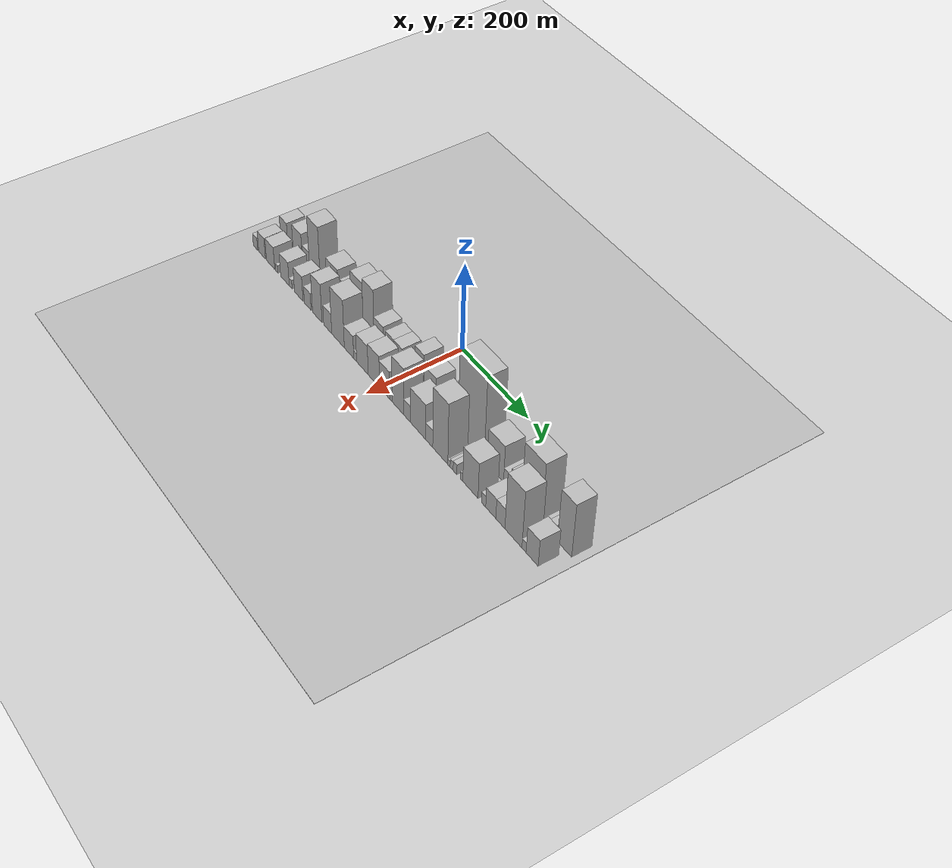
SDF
<?xml version="1.0" encoding="utf-8"?>

<sdf version="1.6">

   <world name="default">

      <gui fullscreen="0">

         <camera name="user_camera">

            <pose>-15 0 4.57585 0 0 0</pose>

            <view_controller>orbit</view_controller>

         </camera>

      </gui>

      <scene>

         <sky>

           <clouds>

             <speed>12</speed>

           </clouds>

         </sky>

         <ambient>0.4 0.4 0.4 1</ambient>

         <background>0.7 0.7 0.7 1</background>

         <shadows>1</shadows>

      </scene>

      <gravity>0 0 -9.8066</gravity>

      <magnetic_field>6e-06 2.3e-05 -4.2e-05</magnetic_field>

      <physics default="0" name="default_physics" type="ode">

         <ode>

            <solver>

               <type>quick</type>

               <iters>10</iters>

               <sor>1.0</sor>

               <use_dynamic_moi_rescaling>0</use_dynamic_moi_rescaling>

            </solver>

            <constraints>

               <cfm>0</cfm>

               <erp>0.2</erp>

               <contact_max_correcting_vel>100</contact_max_correcting_vel>

               <contact_surface_layer>0.001</contact_surface_layer>

            </constraints>

         </ode>

         <max_step_size>0.004</max_step_size>

         <real_time_factor>1</real_time_factor>

         <real_time_update_rate>250</real_time_update_rate>

      </physics>

      <light name="sun" type="directional">

         <cast_shadows>1</cast_shadows>

         <pose>0 0 10 0 0 0</pose>

         <diffuse>0.8 0.8 0.8 1</diffuse>

         <specular>0.2 0.2 0.2 1</specular>

         <attenuation>

            <range>1000</range>

            <constant>0.9</constant>

            <linear>0.01</linear>

            <quadratic>0.001</quadratic>

         </attenuation>

         <direction>-0.5 0.1 -0.9</direction>

      </light>

      <include>

         <name>ground_plane_1</name>

         <uri>model://HANNAS_ground_plane</uri>

         <pose>0 0 0  0 0 0</pose>

      </include>

      <include>

         <name>ground_plane_2</name>

         <uri>model://HANNAS_ground_plane</uri>

         <pose>100 0 0  0 0 0</pose>

      </include>

      <model name="building_1">

         <static>1</static>

         <pose frame="">100.0000 -446.0445 0 0.000000 0.000000 0.000000</pose>

         <link name="link">

            <pose frame="">0 0 9.00 0 0 0</pose>

            <collision name="collision">

               <geometry>

                  <box>

                     <size>40.0000 7.9111 18.0000</size>

                  </box>

               </geometry>

               <max_contacts>10</max_contacts>

               <surface>

                  <contact>

                     <ode/>

                  </contact>

                  <bounce/>

                  <friction>

                     <torsional>

                        <ode/>

                     </torsional>

                     <ode/>

                  </friction>

               </surface>

            </collision>

            <visual name="visual">

               <cast_shadows>0</cast_shadows>

               <geometry>

                  <box>

                     <size>40.0000 7.9111 18.0000</size>

                  </box>

               </geometry>

               <material>

                  <script>

                     <uri>model://HANNAS_wall/materials/scripts</uri>

                     <uri>model://HANNAS_wall/materials/textures</uri>

                     <name>vrc/HANNAS_wall</name>

                  </script>

               </material>

            </visual>

            <self_collide>0</self_collide>

            <enable_wind>0</enable_wind>

            <kinematic>0</kinematic>

         </link>

      </model>

      <model name="building_2">

         <static>1</static>

         <pose frame="">100.0000 -428.3742 0 0.000000 0.000000 0.000000</pose>

         <link name="link">

            <pose frame="">0 0 27.00 0 0 0</pose>

            <collision name="collision">

               <geometry>

                  <box>

                     <size>40.0000 27.4295 54.0000</size>

                  </box>

               </geometry>

               <max_contacts>10</max_contacts>

               <surface>

                  <contact>

                     <ode/>

                  </contact>

                  <bounce/>

                  <friction>

                     <torsional>

                        <ode/>

                     </torsional>

                     <ode/>

                  </friction>

               </surface>

            </collision>

            <visual name="visual">

               <cast_shadows>0</cast_shadows>

               <geometry>

                  <box>

                     <size>40.0000 27.4295 54.0000</size>

                  </box>

               </geometry>

               <material>

                  <script>

                     <uri>model://HANNAS_wall/materials/scripts</uri>

                     <uri>model://HANNAS_wall/materials/textures</uri>

                     <name>vrc/HANNAS_wall</name>

                  </script>

               </material>

            </visual>

            <self_collide>0</self_collide>

            <enable_wind>0</enable_wind>

            <kinematic>0</kinematic>

         </link>

      </model>

      <model name="building_3">

         <static>1</static>

         <pose frame="">100.0000 -402.0157 0 0.000000 0.000000 0.000000</pose>

         <link name="link">

            <pose frame="">0 0 10.50 0 0 0</pose>

            <collision name="collision">

               <geometry>

                  <box>

                     <size>40.0000 9.2875 21.0000</size>

                  </box>

               </geometry>

               <max_contacts>10</max_contacts>

               <surface>

                  <contact>

                     <ode/>

                  </contact>

                  <bounce/>

                  <friction>

                     <torsional>

                        <ode/>

                     </torsional>

                     <ode/>

                  </friction>

               </surface>

            </collision>

            <visual name="visual">

               <cast_shadows>0</cast_shadows>

               <geometry>

                  <box>

                     <size>40.0000 9.2875 21.0000</size>

                  </box>

               </geometry>

               <material>

                  <script>

                     <uri>model://HANNAS_wall/materials/scripts</uri>

                     <uri>model://HANNAS_wall/materials/textures</uri>

                     <name>vrc/HANNAS_wall</name>

                  </script>

               </material>

            </visual>

            <self_collide>0</self_collide>

            <enable_wind>0</enable_wind>

            <kinematic>0</kinematic>

         </link>

      </model>

      <model name="building_4">

         <static>1</static>

         <pose frame="">100.0000 -377.2498 0 0.000000 0.000000 0.000000</pose>

         <link name="link">

            <pose frame="">0 0 33.00 0 0 0</pose>

            <collision name="collision">

               <geometry>

                  <box>

                     <size>40.0000 34.2443 66.0000</size>

                  </box>

               </geometry>

               <max_contacts>10</max_contacts>

               <surface>

                  <contact>

                     <ode/>

                  </contact>

                  <bounce/>

                  <friction>

                     <torsional>

                        <ode/>

                     </torsional>

                     <ode/>

                  </friction>

               </surface>

            </collision>

            <visual name="visual">

               <cast_shadows>0</cast_shadows>

               <geometry>

                  <box>

                     <size>40.0000 34.2443 66.0000</size>

                  </box>

               </geometry>

               <material>

                  <script>

                     <uri>model://HANNAS_wall/materials/scripts</uri>

                     <uri>model://HANNAS_wall/materials/textures</uri>

                     <name>vrc/HANNAS_wall</name>

                  </script>

               </material>

            </visual>

            <self_collide>0</self_collide>

            <enable_wind>0</enable_wind>

            <kinematic>0</kinematic>

         </link>

      </model>

      <model name="building_5">

         <static>1</static>

         <pose frame="">100.0000 -345.1877 0 0.000000 0.000000 0.000000</pose>

         <link name="link">

            <pose frame="">0 0 21.00 0 0 0</pose>

            <collision name="collision">

               <geometry>

                  <box>

                     <size>40.0000 23.8799 42.0000</size>

                  </box>

               </geometry>

               <max_contacts>10</max_contacts>

               <surface>

                  <contact>

                     <ode/>

                  </contact>

                  <bounce/>

                  <friction>

                     <torsional>

                        <ode/>

                     </torsional>

                     <ode/>

                  </friction>

               </surface>

            </collision>

            <visual name="visual">

               <cast_shadows>0</cast_shadows>

               <geometry>

                  <box>

                     <size>40.0000 23.8799 42.0000</size>

                  </box>

               </geometry>

               <material>

                  <script>

                     <uri>model://HANNAS_wall/materials/scripts</uri>

                     <uri>model://HANNAS_wall/materials/textures</uri>

                     <name>vrc/HANNAS_wall</name>

                  </script>

               </material>

            </visual>

            <self_collide>0</self_collide>

            <enable_wind>0</enable_wind>

            <kinematic>0</kinematic>

         </link>

      </model>

      <model name="building_6">

         <static>1</static>

         <pose frame="">100.0000 -313.8028 0 0.000000 0.000000 0.000000</pose>

         <link name="link">

            <pose frame="">0 0 64.50 0 0 0</pose>

            <collision name="collision">

               <geometry>

                  <box>

                     <size>40.0000 38.8897 129.0000</size>

                  </box>

               </geometry>

               <max_contacts>10</max_contacts>

               <surface>

                  <contact>

                     <ode/>

                  </contact>

                  <bounce/>

                  <friction>

                     <torsional>

                        <ode/>

                     </torsional>

                     <ode/>

                  </friction>

               </surface>

            </collision>

            <visual name="visual">

               <cast_shadows>0</cast_shadows>

               <geometry>

                  <box>

                     <size>40.0000 38.8897 129.0000</size>

                  </box>

               </geometry>

               <material>

                  <script>

                     <uri>model://HANNAS_wall/materials/scripts</uri>

                     <uri>model://HANNAS_wall/materials/textures</uri>

                     <name>vrc/HANNAS_wall</name>

                  </script>

               </material>

            </visual>

            <self_collide>0</self_collide>

            <enable_wind>0</enable_wind>

            <kinematic>0</kinematic>

         </link>

      </model>

      <model name="building_7">

         <static>1</static>

         <pose frame="">100.0000 -285.6322 0 0.000000 0.000000 0.000000</pose>

         <link name="link">

            <pose frame="">0 0 13.50 0 0 0</pose>

            <collision name="collision">

               <geometry>

                  <box>

                     <size>40.0000 11.4515 27.0000</size>

                  </box>

               </geometry>

               <max_contacts>10</max_contacts>

               <surface>

                  <contact>

                     <ode/>

                  </contact>

                  <bounce/>

                  <friction>

                     <torsional>

                        <ode/>

                     </torsional>

                     <ode/>

                  </friction>

               </surface>

            </collision>

            <visual name="visual">

               <cast_shadows>0</cast_shadows>

               <geometry>

                  <box>

                     <size>40.0000 11.4515 27.0000</size>

                  </box>

               </geometry>

               <material>

                  <script>

                     <uri>model://HANNAS_wall/materials/scripts</uri>

                     <uri>model://HANNAS_wall/materials/textures</uri>

                     <name>vrc/HANNAS_wall</name>

                  </script>

               </material>

            </visual>

            <self_collide>0</self_collide>

            <enable_wind>0</enable_wind>

            <kinematic>0</kinematic>

         </link>

      </model>

      <model name="building_8">

         <static>1</static>

         <pose frame="">100.0000 -249.8917 0 0.000000 0.000000 0.000000</pose>

         <link name="link">

            <pose frame="">0 0 37.50 0 0 0</pose>

            <collision name="collision">

               <geometry>

                  <box>

                     <size>40.0000 42.0296 75.0000</size>

                  </box>

               </geometry>

               <max_contacts>10</max_contacts>

               <surface>

                  <contact>

                     <ode/>

                  </contact>

                  <bounce/>

                  <friction>

                     <torsional>

                        <ode/>

                     </torsional>

                     <ode/>

                  </friction>

               </surface>

            </collision>

            <visual name="visual">

               <cast_shadows>0</cast_shadows>

               <geometry>

                  <box>

                     <size>40.0000 42.0296 75.0000</size>

                  </box>

               </geometry>

               <material>

                  <script>

                     <uri>model://HANNAS_wall/materials/scripts</uri>

                     <uri>model://HANNAS_wall/materials/textures</uri>

                     <name>vrc/HANNAS_wall</name>

                  </script>

               </material>

            </visual>

            <self_collide>0</self_collide>

            <enable_wind>0</enable_wind>

            <kinematic>0</kinematic>

         </link>

      </model>

      <model name="building_9">

         <static>1</static>

         <pose frame="">100.0000 -203.7269 0 0.000000 0.000000 0.000000</pose>

         <link name="link">

            <pose frame="">0 0 30.00 0 0 0</pose>

            <collision name="collision">

               <geometry>

                  <box>

                     <size>40.0000 34.3001 60.0000</size>

                  </box>

               </geometry>

               <max_contacts>10</max_contacts>

               <surface>

                  <contact>

                     <ode/>

                  </contact>

                  <bounce/>

                  <friction>

                     <torsional>

                        <ode/>

                     </torsional>

                     <ode/>

                  </friction>

               </surface>

            </collision>

            <visual name="visual">

               <cast_shadows>0</cast_shadows>

               <geometry>

                  <box>

                     <size>40.0000 34.3001 60.0000</size>

                  </box>

               </geometry>

               <material>

                  <script>

                     <uri>model://HANNAS_wall/materials/scripts</uri>

                     <uri>model://HANNAS_wall/materials/textures</uri>

                     <name>vrc/HANNAS_wall</name>

                  </script>

               </material>

            </visual>

            <self_collide>0</self_collide>

            <enable_wind>0</enable_wind>

            <kinematic>0</kinematic>

         </link>

      </model>

      <model name="building_10">

         <static>1</static>

         <pose frame="">100.0000 -163.1283 0 0.000000 0.000000 0.000000</pose>

         <link name="link">

            <pose frame="">0 0 54.00 0 0 0</pose>

            <collision name="collision">

               <geometry>

                  <box>

                     <size>40.0000 40.8971 108.0000</size>

                  </box>

               </geometry>

               <max_contacts>10</max_contacts>

               <surface>

                  <contact>

                     <ode/>

                  </contact>

                  <bounce/>

                  <friction>

                     <torsional>

                        <ode/>

                     </torsional>

                     <ode/>

                  </friction>

               </surface>

            </collision>

            <visual name="visual">

               <cast_shadows>0</cast_shadows>

               <geometry>

                  <box>

                     <size>40.0000 40.8971 108.0000</size>

                  </box>

               </geometry>

               <material>

                  <script>

                     <uri>model://HANNAS_wall/materials/scripts</uri>

                     <uri>model://HANNAS_wall/materials/textures</uri>

                     <name>vrc/HANNAS_wall</name>

                  </script>

               </material>

            </visual>

            <self_collide>0</self_collide>

            <enable_wind>0</enable_wind>

            <kinematic>0</kinematic>

         </link>

      </model>

      <model name="building_11">

         <static>1</static>

         <pose frame="">100.0000 -124.2831 0 0.000000 0.000000 0.000000</pose>

         <link name="link">

            <pose frame="">0 0 60.00 0 0 0</pose>

            <collision name="collision">

               <geometry>

                  <box>

                     <size>40.0000 36.7932 120.0000</size>

                  </box>

               </geometry>

               <max_contacts>10</max_contacts>

               <surface>

                  <contact>

                     <ode/>

                  </contact>

                  <bounce/>

                  <friction>

                     <torsional>

                        <ode/>

                     </torsional>

                     <ode/>

                  </friction>

               </surface>

            </collision>

            <visual name="visual">

               <cast_shadows>0</cast_shadows>

               <geometry>

                  <box>

                     <size>40.0000 36.7932 120.0000</size>

                  </box>

               </geometry>

               <material>

                  <script>

                     <uri>model://HANNAS_wall/materials/scripts</uri>

                     <uri>model://HANNAS_wall/materials/textures</uri>

                     <name>vrc/HANNAS_wall</name>

                  </script>

               </material>

            </visual>

            <self_collide>0</self_collide>

            <enable_wind>0</enable_wind>

            <kinematic>0</kinematic>

         </link>

      </model>

      <model name="building_12">

         <static>1</static>

         <pose frame="">100.0000 -90.0963 0 0.000000 0.000000 0.000000</pose>

         <link name="link">

            <pose frame="">0 0 28.50 0 0 0</pose>

            <collision name="collision">

               <geometry>

                  <box>

                     <size>40.0000 31.5804 57.0000</size>

                  </box>

               </geometry>

               <max_contacts>10</max_contacts>

               <surface>

                  <contact>

                     <ode/>

                  </contact>

                  <bounce/>

                  <friction>

                     <torsional>

                        <ode/>

                     </torsional>

                     <ode/>

                  </friction>

               </surface>

            </collision>

            <visual name="visual">

               <cast_shadows>0</cast_shadows>

               <geometry>

                  <box>

                     <size>40.0000 31.5804 57.0000</size>

                  </box>

               </geometry>

               <material>

                  <script>

                     <uri>model://HANNAS_wall/materials/scripts</uri>

                     <uri>model://HANNAS_wall/materials/textures</uri>

                     <name>vrc/HANNAS_wall</name>

                  </script>

               </material>

            </visual>

            <self_collide>0</self_collide>

            <enable_wind>0</enable_wind>

            <kinematic>0</kinematic>

         </link>

      </model>

      <model name="building_13">

         <static>1</static>

         <pose frame="">100.0000 -53.7954 0 0.000000 0.000000 0.000000</pose>

         <link name="link">

            <pose frame="">0 0 27.00 0 0 0</pose>

            <collision name="collision">

               <geometry>

                  <box>

                     <size>40.0000 27.0213 54.0000</size>

                  </box>

               </geometry>

               <max_contacts>10</max_contacts>

               <surface>

                  <contact>

                     <ode/>

                  </contact>

                  <bounce/>

                  <friction>

                     <torsional>

                        <ode/>

                     </torsional>

                     <ode/>

                  </friction>

               </surface>

            </collision>

            <visual name="visual">

               <cast_shadows>0</cast_shadows>

               <geometry>

                  <box>

                     <size>40.0000 27.0213 54.0000</size>

                  </box>

               </geometry>

               <material>

                  <script>

                     <uri>model://HANNAS_wall/materials/scripts</uri>

                     <uri>model://HANNAS_wall/materials/textures</uri>

                     <name>vrc/HANNAS_wall</name>

                  </script>

               </material>

            </visual>

            <self_collide>0</self_collide>

            <enable_wind>0</enable_wind>

            <kinematic>0</kinematic>

         </link>

      </model>

      <model name="building_14">

         <static>1</static>

         <pose frame="">100.0000 -26.3035 0 0.000000 0.000000 0.000000</pose>

         <link name="link">

            <pose frame="">0 0 27.00 0 0 0</pose>

            <collision name="collision">

               <geometry>

                  <box>

                     <size>40.0000 27.9625 54.0000</size>

                  </box>

               </geometry>

               <max_contacts>10</max_contacts>

               <surface>

                  <contact>

                     <ode/>

                  </contact>

                  <bounce/>

                  <friction>

                     <torsional>

                        <ode/>

                     </torsional>

                     <ode/>

                  </friction>

               </surface>

            </collision>

            <visual name="visual">

               <cast_shadows>0</cast_shadows>

               <geometry>

                  <box>

                     <size>40.0000 27.9625 54.0000</size>

                  </box>

               </geometry>

               <material>

                  <script>

                     <uri>model://HANNAS_wall/materials/scripts</uri>

                     <uri>model://HANNAS_wall/materials/textures</uri>

                     <name>vrc/HANNAS_wall</name>

                  </script>

               </material>

            </visual>

            <self_collide>0</self_collide>

            <enable_wind>0</enable_wind>

            <kinematic>0</kinematic>

         </link>

      </model>

      <model name="building_15">

         <static>1</static>

         <pose frame="">100.0000 6.3025 0 0.000000 0.000000 0.000000</pose>

         <link name="link">

            <pose frame="">0 0 24.00 0 0 0</pose>

            <collision name="collision">

               <geometry>

                  <box>

                     <size>40.0000 27.2494 48.0000</size>

                  </box>

               </geometry>

               <max_contacts>10</max_contacts>

               <surface>

                  <contact>

                     <ode/>

                  </contact>

                  <bounce/>

                  <friction>

                     <torsional>

                        <ode/>

                     </torsional>

                     <ode/>

                  </friction>

               </surface>

            </collision>

            <visual name="visual">

               <cast_shadows>0</cast_shadows>

               <geometry>

                  <box>

                     <size>40.0000 27.2494 48.0000</size>

                  </box>

               </geometry>

               <material>

                  <script>

                     <uri>model://HANNAS_wall/materials/scripts</uri>

                     <uri>model://HANNAS_wall/materials/textures</uri>

                     <name>vrc/HANNAS_wall</name>

                  </script>

               </material>

            </visual>

            <self_collide>0</self_collide>

            <enable_wind>0</enable_wind>

            <kinematic>0</kinematic>

         </link>

      </model>

      <model name="building_16">

         <static>1</static>

         <pose frame="">100.0000 24.2655 0 0.000000 0.000000 0.000000</pose>

         <link name="link">

            <pose frame="">0 0 9.00 0 0 0</pose>

            <collision name="collision">

               <geometry>

                  <box>

                     <size>40.0000 8.6766 18.0000</size>

                  </box>

               </geometry>

               <max_contacts>10</max_contacts>

               <surface>

                  <contact>

                     <ode/>

                  </contact>

                  <bounce/>

                  <friction>

                     <torsional>

                        <ode/>

                     </torsional>

                     <ode/>

                  </friction>

               </surface>

            </collision>

            <visual name="visual">

               <cast_shadows>0</cast_shadows>

               <geometry>

                  <box>

                     <size>40.0000 8.6766 18.0000</size>

                  </box>

               </geometry>

               <material>

                  <script>

                     <uri>model://HANNAS_wall/materials/scripts</uri>

                     <uri>model://HANNAS_wall/materials/textures</uri>

                     <name>vrc/HANNAS_wall</name>

                  </script>

               </material>

            </visual>

            <self_collide>0</self_collide>

            <enable_wind>0</enable_wind>

            <kinematic>0</kinematic>

         </link>

      </model>

      <model name="building_17">

         <static>1</static>

         <pose frame="">100.0000 43.0093 0 0.000000 0.000000 0.000000</pose>

         <link name="link">

            <pose frame="">0 0 48.00 0 0 0</pose>

            <collision name="collision">

               <geometry>

                  <box>

                     <size>40.0000 28.8110 96.0000</size>

                  </box>

               </geometry>

               <max_contacts>10</max_contacts>

               <surface>

                  <contact>

                     <ode/>

                  </contact>

                  <bounce/>

                  <friction>

                     <torsional>

                        <ode/>

                     </torsional>

                     <ode/>

                  </friction>

               </surface>

            </collision>

            <visual name="visual">

               <cast_shadows>0</cast_shadows>

               <geometry>

                  <box>

                     <size>40.0000 28.8110 96.0000</size>

                  </box>

               </geometry>

               <material>

                  <script>

                     <uri>model://HANNAS_wall/materials/scripts</uri>

                     <uri>model://HANNAS_wall/materials/textures</uri>

                     <name>vrc/HANNAS_wall</name>

                  </script>

               </material>

            </visual>

            <self_collide>0</self_collide>

            <enable_wind>0</enable_wind>

            <kinematic>0</kinematic>

         </link>

      </model>

      <model name="building_18">

         <static>1</static>

         <pose frame="">100.0000 76.1650 0 0.000000 0.000000 0.000000</pose>

         <link name="link">

            <pose frame="">0 0 36.00 0 0 0</pose>

            <collision name="collision">

               <geometry>

                  <box>

                     <size>40.0000 37.5004 72.0000</size>

                  </box>

               </geometry>

               <max_contacts>10</max_contacts>

               <surface>

                  <contact>

                     <ode/>

                  </contact>

                  <bounce/>

                  <friction>

                     <torsional>

                        <ode/>

                     </torsional>

                     <ode/>

                  </friction>

               </surface>

            </collision>

            <visual name="visual">

               <cast_shadows>0</cast_shadows>

               <geometry>

                  <box>

                     <size>40.0000 37.5004 72.0000</size>

                  </box>

               </geometry>

               <material>

                  <script>

                     <uri>model://HANNAS_wall/materials/scripts</uri>

                     <uri>model://HANNAS_wall/materials/textures</uri>

                     <name>vrc/HANNAS_wall</name>

                  </script>

               </material>

            </visual>

            <self_collide>0</self_collide>

            <enable_wind>0</enable_wind>

            <kinematic>0</kinematic>

         </link>

      </model>

      <model name="building_19">

         <static>1</static>

         <pose frame="">100.0000 108.5897 0 0.000000 0.000000 0.000000</pose>

         <link name="link">

            <pose frame="">0 0 24.00 0 0 0</pose>

            <collision name="collision">

               <geometry>

                  <box>

                     <size>40.0000 27.3489 48.0000</size>

                  </box>

               </geometry>

               <max_contacts>10</max_contacts>

               <surface>

                  <contact>

                     <ode/>

                  </contact>

                  <bounce/>

                  <friction>

                     <torsional>

                        <ode/>

                     </torsional>

                     <ode/>

                  </friction>

               </surface>

            </collision>

            <visual name="visual">

               <cast_shadows>0</cast_shadows>

               <geometry>

                  <box>

                     <size>40.0000 27.3489 48.0000</size>

                  </box>

               </geometry>

               <material>

                  <script>

                     <uri>model://HANNAS_wall/materials/scripts</uri>

                     <uri>model://HANNAS_wall/materials/textures</uri>

                     <name>vrc/HANNAS_wall</name>

                  </script>

               </material>

            </visual>

            <self_collide>0</self_collide>

            <enable_wind>0</enable_wind>

            <kinematic>0</kinematic>

         </link>

      </model>

      <model name="building_20">

         <static>1</static>

         <pose frame="">100.0000 126.9915 0 0.000000 0.000000 0.000000</pose>

         <link name="link">

            <pose frame="">0 0 10.50 0 0 0</pose>

            <collision name="collision">

               <geometry>

                  <box>

                     <size>40.0000 9.4548 21.0000</size>

                  </box>

               </geometry>

               <max_contacts>10</max_contacts>

               <surface>

                  <contact>

                     <ode/>

                  </contact>

                  <bounce/>

                  <friction>

                     <torsional>

                        <ode/>

                     </torsional>

                     <ode/>

                  </friction>

               </surface>

            </collision>

            <visual name="visual">

               <cast_shadows>0</cast_shadows>

               <geometry>

                  <box>

                     <size>40.0000 9.4548 21.0000</size>

                  </box>

               </geometry>

               <material>

                  <script>

                     <uri>model://HANNAS_wall/materials/scripts</uri>

                     <uri>model://HANNAS_wall/materials/textures</uri>

                     <name>vrc/HANNAS_wall</name>

                  </script>

               </material>

            </visual>

            <self_collide>0</self_collide>

            <enable_wind>0</enable_wind>

            <kinematic>0</kinematic>

         </link>

      </model>

      <model name="building_21">

         <static>1</static>

         <pose frame="">100.0000 147.1534 0 0.000000 0.000000 0.000000</pose>

         <link name="link">

            <pose frame="">0 0 30.00 0 0 0</pose>

            <collision name="collision">

               <geometry>

                  <box>

                     <size>40.0000 30.8690 60.0000</size>

                  </box>

               </geometry>

               <max_contacts>10</max_contacts>

               <surface>

                  <contact>

                     <ode/>

                  </contact>

                  <bounce/>

                  <friction>

                     <torsional>

                        <ode/>

                     </torsional>

                     <ode/>

                  </friction>

               </surface>

            </collision>

            <visual name="visual">

               <cast_shadows>0</cast_shadows>

               <geometry>

                  <box>

                     <size>40.0000 30.8690 60.0000</size>

                  </box>

               </geometry>

               <material>

                  <script>

                     <uri>model://HANNAS_wall/materials/scripts</uri>

                     <uri>model://HANNAS_wall/materials/textures</uri>

                     <name>vrc/HANNAS_wall</name>

                  </script>

               </material>

            </visual>

            <self_collide>0</self_collide>

            <enable_wind>0</enable_wind>

            <kinematic>0</kinematic>

         </link>

      </model>

      <model name="building_22">

         <static>1</static>

         <pose frame="">100.0000 201.8062 0 0.000000 0.000000 0.000000</pose>

         <link name="link">

            <pose frame="">0 0 99.00 0 0 0</pose>

            <collision name="collision">

               <geometry>

                  <box>

                     <size>40.0000 78.4366 198.0000</size>

                  </box>

               </geometry>

               <max_contacts>10</max_contacts>

               <surface>

                  <contact>

                     <ode/>

                  </contact>

                  <bounce/>

                  <friction>

                     <torsional>

                        <ode/>

                     </torsional>

                     <ode/>

                  </friction>

               </surface>

            </collision>

            <visual name="visual">

               <cast_shadows>0</cast_shadows>

               <geometry>

                  <box>

                     <size>40.0000 78.4366 198.0000</size>

                  </box>

               </geometry>

               <material>

                  <script>

                     <uri>model://HANNAS_wall/materials/scripts</uri>

                     <uri>model://HANNAS_wall/materials/textures</uri>

                     <name>vrc/HANNAS_wall</name>

                  </script>

               </material>

            </visual>

            <self_collide>0</self_collide>

            <enable_wind>0</enable_wind>

            <kinematic>0</kinematic>

         </link>

      </model>

      <model name="building_23">

         <static>1</static>

         <pose frame="">100.0000 273.3668 0 0.000000 0.000000 0.000000</pose>

         <link name="link">

            <pose frame="">0 0 43.50 0 0 0</pose>

            <collision name="collision">

               <geometry>

                  <box>

                     <size>40.0000 46.6846 87.0000</size>

                  </box>

               </geometry>

               <max_contacts>10</max_contacts>

               <surface>

                  <contact>

                     <ode/>

                  </contact>

                  <bounce/>

                  <friction>

                     <torsional>

                        <ode/>

                     </torsional>

                     <ode/>

                  </friction>

               </surface>

            </collision>

            <visual name="visual">

               <cast_shadows>0</cast_shadows>

               <geometry>

                  <box>

                     <size>40.0000 46.6846 87.0000</size>

                  </box>

               </geometry>

               <material>

                  <script>

                     <uri>model://HANNAS_wall/materials/scripts</uri>

                     <uri>model://HANNAS_wall/materials/textures</uri>

                     <name>vrc/HANNAS_wall</name>

                  </script>

               </material>

            </visual>

            <self_collide>0</self_collide>

            <enable_wind>0</enable_wind>

            <kinematic>0</kinematic>

         </link>

      </model>

      <model name="building_24">

         <static>1</static>

         <pose frame="">100.0000 307.2393 0 0.000000 0.000000 0.000000</pose>

         <link name="link">

            <pose frame="">0 0 18.00 0 0 0</pose>

            <collision name="collision">

               <geometry>

                  <box>

                     <size>40.0000 21.0604 36.0000</size>

                  </box>

               </geometry>

               <max_contacts>10</max_contacts>

               <surface>

                  <contact>

                     <ode/>

                  </contact>

                  <bounce/>

                  <friction>

                     <torsional>

                        <ode/>

                     </torsional>

                     <ode/>

                  </friction>

               </surface>

            </collision>

            <visual name="visual">

               <cast_shadows>0</cast_shadows>

               <geometry>

                  <box>

                     <size>40.0000 21.0604 36.0000</size>

                  </box>

               </geometry>

               <material>

                  <script>

                     <uri>model://HANNAS_wall/materials/scripts</uri>

                     <uri>model://HANNAS_wall/materials/textures</uri>

                     <name>vrc/HANNAS_wall</name>

                  </script>

               </material>

            </visual>

            <self_collide>0</self_collide>

            <enable_wind>0</enable_wind>

            <kinematic>0</kinematic>

         </link>

      </model>

      <model name="building_25">

         <static>1</static>

         <pose frame="">100.0000 332.6892 0 0.000000 0.000000 0.000000</pose>

         <link name="link">

            <pose frame="">0 0 27.00 0 0 0</pose>

            <collision name="collision">

               <geometry>

                  <box>

                     <size>40.0000 29.8393 54.0000</size>

                  </box>

               </geometry>

               <max_contacts>10</max_contacts>

               <surface>

                  <contact>

                     <ode/>

                  </contact>

                  <bounce/>

                  <friction>

                     <torsional>

                        <ode/>

                     </torsional>

                     <ode/>

                  </friction>

               </surface>

            </collision>

            <visual name="visual">

               <cast_shadows>0</cast_shadows>

               <geometry>

                  <box>

                     <size>40.0000 29.8393 54.0000</size>

                  </box>

               </geometry>

               <material>

                  <script>

                     <uri>model://HANNAS_wall/materials/scripts</uri>

                     <uri>model://HANNAS_wall/materials/textures</uri>

                     <name>vrc/HANNAS_wall</name>

                  </script>

               </material>

            </visual>

            <self_collide>0</self_collide>

            <enable_wind>0</enable_wind>

            <kinematic>0</kinematic>

         </link>

      </model>

      <model name="building_26">

         <static>1</static>

         <pose frame="">100.0000 375.5573 0 0.000000 0.000000 0.000000</pose>

         <link name="link">

            <pose frame="">0 0 72.00 0 0 0</pose>

            <collision name="collision">

               <geometry>

                  <box>

                     <size>40.0000 55.8970 144.0000</size>

                  </box>

               </geometry>

               <max_contacts>10</max_contacts>

               <surface>

                  <contact>

                     <ode/>

                  </contact>

                  <bounce/>

                  <friction>

                     <torsional>

                        <ode/>

                     </torsional>

                     <ode/>

                  </friction>

               </surface>

            </collision>

            <visual name="visual">

               <cast_shadows>0</cast_shadows>

               <geometry>

                  <box>

                     <size>40.0000 55.8970 144.0000</size>

                  </box>

               </geometry>

               <material>

                  <script>

                     <uri>model://HANNAS_wall/materials/scripts</uri>

                     <uri>model://HANNAS_wall/materials/textures</uri>

                     <name>vrc/HANNAS_wall</name>

                  </script>

               </material>

            </visual>

            <self_collide>0</self_collide>

            <enable_wind>0</enable_wind>

            <kinematic>0</kinematic>

         </link>

      </model>

      <model name="building_27">

         <static>1</static>

         <pose frame="">100.0000 415.6739 0 0.000000 0.000000 0.000000</pose>

         <link name="link">

            <pose frame="">0 0 12.00 0 0 0</pose>

            <collision name="collision">

               <geometry>

                  <box>

                     <size>40.0000 10.3362 24.0000</size>

                  </box>

               </geometry>

               <max_contacts>10</max_contacts>

               <surface>

                  <contact>

                     <ode/>

                  </contact>

                  <bounce/>

                  <friction>

                     <torsional>

                        <ode/>

                     </torsional>

                     <ode/>

                  </friction>

               </surface>

            </collision>

            <visual name="visual">

               <cast_shadows>0</cast_shadows>

               <geometry>

                  <box>

                     <size>40.0000 10.3362 24.0000</size>

                  </box>

               </geometry>

               <material>

                  <script>

                     <uri>model://HANNAS_wall/materials/scripts</uri>

                     <uri>model://HANNAS_wall/materials/textures</uri>

                     <name>vrc/HANNAS_wall</name>

                  </script>

               </material>

            </visual>

            <self_collide>0</self_collide>

            <enable_wind>0</enable_wind>

            <kinematic>0</kinematic>

         </link>

      </model>

      <model name="building_28">

         <static>1</static>

         <pose frame="">100.0000 432.2948 0 0.000000 0.000000 0.000000</pose>

         <link name="link">

            <pose frame="">0 0 16.50 0 0 0</pose>

            <collision name="collision">

               <geometry>

                  <box>

                     <size>40.0000 16.9056 33.0000</size>

                  </box>

               </geometry>

               <max_contacts>10</max_contacts>

               <surface>

                  <contact>

                     <ode/>

                  </contact>

                  <bounce/>

                  <friction>

                     <torsional>

                        <ode/>

                     </torsional>

                     <ode/>

                  </friction>

               </surface>

            </collision>

            <visual name="visual">

               <cast_shadows>0</cast_shadows>

               <geometry>

                  <box>

                     <size>40.0000 16.9056 33.0000</size>

                  </box>

               </geometry>

               <material>

                  <script>

                     <uri>model://HANNAS_wall/materials/scripts</uri>

                     <uri>model://HANNAS_wall/materials/textures</uri>

                     <name>vrc/HANNAS_wall</name>

                  </script>

               </material>

            </visual>

            <self_collide>0</self_collide>

            <enable_wind>0</enable_wind>

            <kinematic>0</kinematic>

         </link>

      </model>

      <model name="building_29">

         <static>1</static>

         <pose frame="">100.0000 464.8829 0 0.000000 0.000000 0.000000</pose>

         <link name="link">

            <pose frame="">0 0 63.00 0 0 0</pose>

            <collision name="collision">

               <geometry>

                  <box>

                     <size>40.0000 38.2706 126.0000</size>

                  </box>

               </geometry>

               <max_contacts>10</max_contacts>

               <surface>

                  <contact>

                     <ode/>

                  </contact>

                  <bounce/>

                  <friction>

                     <torsional>

                        <ode/>

                     </torsional>

                     <ode/>

                  </friction>

               </surface>

            </collision>

            <visual name="visual">

               <cast_shadows>0</cast_shadows>

               <geometry>

                  <box>

                     <size>40.0000 38.2706 126.0000</size>

                  </box>

               </geometry>

               <material>

                  <script>

                     <uri>model://HANNAS_wall/materials/scripts</uri>

                     <uri>model://HANNAS_wall/materials/textures</uri>

                     <name>vrc/HANNAS_wall</name>

                  </script>

               </material>

            </visual>

            <self_collide>0</self_collide>

            <enable_wind>0</enable_wind>

            <kinematic>0</kinematic>

         </link>

      </model>

      <model name="building_30">

         <static>1</static>

         <pose frame="">155.0000 -441.4879 0 0.000000 0.000000 0.000000</pose>

         <link name="link">

            <pose frame="">0 0 15.00 0 0 0</pose>

            <collision name="collision">

               <geometry>

                  <box>

                     <size>40.0000 17.0242 30.0000</size>

                  </box>

               </geometry>

               <max_contacts>10</max_contacts>

               <surface>

                  <contact>

                     <ode/>

                  </contact>

                  <bounce/>

                  <friction>

                     <torsional>

                        <ode/>

                     </torsional>

                     <ode/>

                  </friction>

               </surface>

            </collision>

            <visual name="visual">

               <cast_shadows>0</cast_shadows>

               <geometry>

                  <box>

                     <size>40.0000 17.0242 30.0000</size>

                  </box>

               </geometry>

               <material>

                  <script>

                     <uri>model://HANNAS_wall/materials/scripts</uri>

                     <uri>model://HANNAS_wall/materials/textures</uri>

                     <name>vrc/HANNAS_wall</name>

                  </script>

               </material>

            </visual>

            <self_collide>0</self_collide>

            <enable_wind>0</enable_wind>

            <kinematic>0</kinematic>

         </link>

      </model>

      <model name="building_31">

         <static>1</static>

         <pose frame="">155.0000 -416.0695 0 0.000000 0.000000 0.000000</pose>

         <link name="link">

            <pose frame="">0 0 25.50 0 0 0</pose>

            <collision name="collision">

               <geometry>

                  <box>

                     <size>40.0000 25.8125 51.0000</size>

                  </box>

               </geometry>

               <max_contacts>10</max_contacts>

               <surface>

                  <contact>

                     <ode/>

                  </contact>

                  <bounce/>

                  <friction>

                     <torsional>

                        <ode/>

                     </torsional>

                     <ode/>

                  </friction>

               </surface>

            </collision>

            <visual name="visual">

               <cast_shadows>0</cast_shadows>

               <geometry>

                  <box>

                     <size>40.0000 25.8125 51.0000</size>

                  </box>

               </geometry>

               <material>

                  <script>

                     <uri>model://HANNAS_wall/materials/scripts</uri>

                     <uri>model://HANNAS_wall/materials/textures</uri>

                     <name>vrc/HANNAS_wall</name>

                  </script>

               </material>

            </visual>

            <self_collide>0</self_collide>

            <enable_wind>0</enable_wind>

            <kinematic>0</kinematic>

         </link>

      </model>

      <model name="building_32">

         <static>1</static>

         <pose frame="">155.0000 -383.4789 0 0.000000 0.000000 0.000000</pose>

         <link name="link">

            <pose frame="">0 0 27.00 0 0 0</pose>

            <collision name="collision">

               <geometry>

                  <box>

                     <size>40.0000 31.3688 54.0000</size>

                  </box>

               </geometry>

               <max_contacts>10</max_contacts>

               <surface>

                  <contact>

                     <ode/>

                  </contact>

                  <bounce/>

                  <friction>

                     <torsional>

                        <ode/>

                     </torsional>

                     <ode/>

                  </friction>

               </surface>

            </collision>

            <visual name="visual">

               <cast_shadows>0</cast_shadows>

               <geometry>

                  <box>

                     <size>40.0000 31.3688 54.0000</size>

                  </box>

               </geometry>

               <material>

                  <script>

                     <uri>model://HANNAS_wall/materials/scripts</uri>

                     <uri>model://HANNAS_wall/materials/textures</uri>

                     <name>vrc/HANNAS_wall</name>

                  </script>

               </material>

            </visual>

            <self_collide>0</self_collide>

            <enable_wind>0</enable_wind>

            <kinematic>0</kinematic>

         </link>

      </model>

      <model name="building_33">

         <static>1</static>

         <pose frame="">155.0000 -359.7463 0 0.000000 0.000000 0.000000</pose>

         <link name="link">

            <pose frame="">0 0 9.00 0 0 0</pose>

            <collision name="collision">

               <geometry>

                  <box>

                     <size>40.0000 8.0962 18.0000</size>

                  </box>

               </geometry>

               <max_contacts>10</max_contacts>

               <surface>

                  <contact>

                     <ode/>

                  </contact>

                  <bounce/>

                  <friction>

                     <torsional>

                        <ode/>

                     </torsional>

                     <ode/>

                  </friction>

               </surface>

            </collision>

            <visual name="visual">

               <cast_shadows>0</cast_shadows>

               <geometry>

                  <box>

                     <size>40.0000 8.0962 18.0000</size>

                  </box>

               </geometry>

               <material>

                  <script>

                     <uri>model://HANNAS_wall/materials/scripts</uri>

                     <uri>model://HANNAS_wall/materials/textures</uri>

                     <name>vrc/HANNAS_wall</name>

                  </script>

               </material>

            </visual>

            <self_collide>0</self_collide>

            <enable_wind>0</enable_wind>

            <kinematic>0</kinematic>

         </link>

      </model>

      <model name="building_34">

         <static>1</static>

         <pose frame="">155.0000 -329.5997 0 0.000000 0.000000 0.000000</pose>

         <link name="link">

            <pose frame="">0 0 28.50 0 0 0</pose>

            <collision name="collision">

               <geometry>

                  <box>

                     <size>40.0000 32.1970 57.0000</size>

                  </box>

               </geometry>

               <max_contacts>10</max_contacts>

               <surface>

                  <contact>

                     <ode/>

                  </contact>

                  <bounce/>

                  <friction>

                     <torsional>

                        <ode/>

                     </torsional>

                     <ode/>

                  </friction>

               </surface>

            </collision>

            <visual name="visual">

               <cast_shadows>0</cast_shadows>

               <geometry>

                  <box>

                     <size>40.0000 32.1970 57.0000</size>

                  </box>

               </geometry>

               <material>

                  <script>

                     <uri>model://HANNAS_wall/materials/scripts</uri>

                     <uri>model://HANNAS_wall/materials/textures</uri>

                     <name>vrc/HANNAS_wall</name>

                  </script>

               </material>

            </visual>

            <self_collide>0</self_collide>

            <enable_wind>0</enable_wind>

            <kinematic>0</kinematic>

         </link>

      </model>

      <model name="building_35">

         <static>1</static>

         <pose frame="">155.0000 -308.3166 0 0.000000 0.000000 0.000000</pose>

         <link name="link">

            <pose frame="">0 0 10.50 0 0 0</pose>

            <collision name="collision">

               <geometry>

                  <box>

                     <size>40.0000 10.3693 21.0000</size>

                  </box>

               </geometry>

               <max_contacts>10</max_contacts>

               <surface>

                  <contact>

                     <ode/>

                  </contact>

                  <bounce/>

                  <friction>

                     <torsional>

                        <ode/>

                     </torsional>

                     <ode/>

                  </friction>

               </surface>

            </collision>

            <visual name="visual">

               <cast_shadows>0</cast_shadows>

               <geometry>

                  <box>

                     <size>40.0000 10.3693 21.0000</size>

                  </box>

               </geometry>

               <material>

                  <script>

                     <uri>model://HANNAS_wall/materials/scripts</uri>

                     <uri>model://HANNAS_wall/materials/textures</uri>

                     <name>vrc/HANNAS_wall</name>

                  </script>

               </material>

            </visual>

            <self_collide>0</self_collide>

            <enable_wind>0</enable_wind>

            <kinematic>0</kinematic>

         </link>

      </model>

      <model name="building_36">

         <static>1</static>

         <pose frame="">155.0000 -278.6111 0 0.000000 0.000000 0.000000</pose>

         <link name="link">

            <pose frame="">0 0 30.00 0 0 0</pose>

            <collision name="collision">

               <geometry>

                  <box>

                     <size>40.0000 31.0417 60.0000</size>

                  </box>

               </geometry>

               <max_contacts>10</max_contacts>

               <surface>

                  <contact>

                     <ode/>

                  </contact>

                  <bounce/>

                  <friction>

                     <torsional>

                        <ode/>

                     </torsional>

                     <ode/>

                  </friction>

               </surface>

            </collision>

            <visual name="visual">

               <cast_shadows>0</cast_shadows>

               <geometry>

                  <box>

                     <size>40.0000 31.0417 60.0000</size>

                  </box>

               </geometry>

               <material>

                  <script>

                     <uri>model://HANNAS_wall/materials/scripts</uri>

                     <uri>model://HANNAS_wall/materials/textures</uri>

                     <name>vrc/HANNAS_wall</name>

                  </script>

               </material>

            </visual>

            <self_collide>0</self_collide>

            <enable_wind>0</enable_wind>

            <kinematic>0</kinematic>

         </link>

      </model>

      <model name="building_37">

         <static>1</static>

         <pose frame="">155.0000 -245.9756 0 0.000000 0.000000 0.000000</pose>

         <link name="link">

            <pose frame="">0 0 21.00 0 0 0</pose>

            <collision name="collision">

               <geometry>

                  <box>

                     <size>40.0000 24.2291 42.0000</size>

                  </box>

               </geometry>

               <max_contacts>10</max_contacts>

               <surface>

                  <contact>

                     <ode/>

                  </contact>

                  <bounce/>

                  <friction>

                     <torsional>

                        <ode/>

                     </torsional>

                     <ode/>

                  </friction>

               </surface>

            </collision>

            <visual name="visual">

               <cast_shadows>0</cast_shadows>

               <geometry>

                  <box>

                     <size>40.0000 24.2291 42.0000</size>

                  </box>

               </geometry>

               <material>

                  <script>

                     <uri>model://HANNAS_wall/materials/scripts</uri>

                     <uri>model://HANNAS_wall/materials/textures</uri>

                     <name>vrc/HANNAS_wall</name>

                  </script>

               </material>

            </visual>

            <self_collide>0</self_collide>

            <enable_wind>0</enable_wind>

            <kinematic>0</kinematic>

         </link>

      </model>

      <model name="building_38">

         <static>1</static>

         <pose frame="">155.0000 -211.9666 0 0.000000 0.000000 0.000000</pose>

         <link name="link">

            <pose frame="">0 0 46.50 0 0 0</pose>

            <collision name="collision">

               <geometry>

                  <box>

                     <size>40.0000 33.7891 93.0000</size>

                  </box>

               </geometry>

               <max_contacts>10</max_contacts>

               <surface>

                  <contact>

                     <ode/>

                  </contact>

                  <bounce/>

                  <friction>

                     <torsional>

                        <ode/>

                     </torsional>

                     <ode/>

                  </friction>

               </surface>

            </collision>

            <visual name="visual">

               <cast_shadows>0</cast_shadows>

               <geometry>

                  <box>

                     <size>40.0000 33.7891 93.0000</size>

                  </box>

               </geometry>

               <material>

                  <script>

                     <uri>model://HANNAS_wall/materials/scripts</uri>

                     <uri>model://HANNAS_wall/materials/textures</uri>

                     <name>vrc/HANNAS_wall</name>

                  </script>

               </material>

            </visual>

            <self_collide>0</self_collide>

            <enable_wind>0</enable_wind>

            <kinematic>0</kinematic>

         </link>

      </model>

      <model name="building_39">

         <static>1</static>

         <pose frame="">155.0000 -175.0666 0 0.000000 0.000000 0.000000</pose>

         <link name="link">

            <pose frame="">0 0 24.00 0 0 0</pose>

            <collision name="collision">

               <geometry>

                  <box>

                     <size>40.0000 28.0108 48.0000</size>

                  </box>

               </geometry>

               <max_contacts>10</max_contacts>

               <surface>

                  <contact>

                     <ode/>

                  </contact>

                  <bounce/>

                  <friction>

                     <torsional>

                        <ode/>

                     </torsional>

                     <ode/>

                  </friction>

               </surface>

            </collision>

            <visual name="visual">

               <cast_shadows>0</cast_shadows>

               <geometry>

                  <box>

                     <size>40.0000 28.0108 48.0000</size>

                  </box>

               </geometry>

               <material>

                  <script>

                     <uri>model://HANNAS_wall/materials/scripts</uri>

                     <uri>model://HANNAS_wall/materials/textures</uri>

                     <name>vrc/HANNAS_wall</name>

                  </script>

               </material>

            </visual>

            <self_collide>0</self_collide>

            <enable_wind>0</enable_wind>

            <kinematic>0</kinematic>

         </link>

      </model>

      <model name="building_40">

         <static>1</static>

         <pose frame="">155.0000 -139.2162 0 0.000000 0.000000 0.000000</pose>

         <link name="link">

            <pose frame="">0 0 57.00 0 0 0</pose>

            <collision name="collision">

               <geometry>

                  <box>

                     <size>40.0000 43.6900 114.0000</size>

                  </box>

               </geometry>

               <max_contacts>10</max_contacts>

               <surface>

                  <contact>

                     <ode/>

                  </contact>

                  <bounce/>

                  <friction>

                     <torsional>

                        <ode/>

                     </torsional>

                     <ode/>

                  </friction>

               </surface>

            </collision>

            <visual name="visual">

               <cast_shadows>0</cast_shadows>

               <geometry>

                  <box>

                     <size>40.0000 43.6900 114.0000</size>

                  </box>

               </geometry>

               <material>

                  <script>

                     <uri>model://HANNAS_wall/materials/scripts</uri>

                     <uri>model://HANNAS_wall/materials/textures</uri>

                     <name>vrc/HANNAS_wall</name>

                  </script>

               </material>

            </visual>

            <self_collide>0</self_collide>

            <enable_wind>0</enable_wind>

            <kinematic>0</kinematic>

         </link>

      </model>

      <model name="building_41">

         <static>1</static>

         <pose frame="">155.0000 -101.5321 0 0.000000 0.000000 0.000000</pose>

         <link name="link">

            <pose frame="">0 0 27.00 0 0 0</pose>

            <collision name="collision">

               <geometry>

                  <box>

                     <size>40.0000 31.6781 54.0000</size>

                  </box>

               </geometry>

               <max_contacts>10</max_contacts>

               <surface>

                  <contact>

                     <ode/>

                  </contact>

                  <bounce/>

                  <friction>

                     <torsional>

                        <ode/>

                     </torsional>

                     <ode/>

                  </friction>

               </surface>

            </collision>

            <visual name="visual">

               <cast_shadows>0</cast_shadows>

               <geometry>

                  <box>

                     <size>40.0000 31.6781 54.0000</size>

                  </box>

               </geometry>

               <material>

                  <script>

                     <uri>model://HANNAS_wall/materials/scripts</uri>

                     <uri>model://HANNAS_wall/materials/textures</uri>

                     <name>vrc/HANNAS_wall</name>

                  </script>

               </material>

            </visual>

            <self_collide>0</self_collide>

            <enable_wind>0</enable_wind>

            <kinematic>0</kinematic>

         </link>

      </model>

      <model name="building_42">

         <static>1</static>

         <pose frame="">155.0000 -80.7195 0 0.000000 0.000000 0.000000</pose>

         <link name="link">

            <pose frame="">0 0 10.50 0 0 0</pose>

            <collision name="collision">

               <geometry>

                  <box>

                     <size>40.0000 9.9471 21.0000</size>

                  </box>

               </geometry>

               <max_contacts>10</max_contacts>

               <surface>

                  <contact>

                     <ode/>

                  </contact>

                  <bounce/>

                  <friction>

                     <torsional>

                        <ode/>

                     </torsional>

                     <ode/>

                  </friction>

               </surface>

            </collision>

            <visual name="visual">

               <cast_shadows>0</cast_shadows>

               <geometry>

                  <box>

                     <size>40.0000 9.9471 21.0000</size>

                  </box>

               </geometry>

               <material>

                  <script>

                     <uri>model://HANNAS_wall/materials/scripts</uri>

                     <uri>model://HANNAS_wall/materials/textures</uri>

                     <name>vrc/HANNAS_wall</name>

                  </script>

               </material>

            </visual>

            <self_collide>0</self_collide>

            <enable_wind>0</enable_wind>

            <kinematic>0</kinematic>

         </link>

      </model>

      <model name="building_43">

         <static>1</static>

         <pose frame="">155.0000 -56.5079 0 0.000000 0.000000 0.000000</pose>

         <link name="link">

            <pose frame="">0 0 34.50 0 0 0</pose>

            <collision name="collision">

               <geometry>

                  <box>

                     <size>40.0000 38.4760 69.0000</size>

                  </box>

               </geometry>

               <max_contacts>10</max_contacts>

               <surface>

                  <contact>

                     <ode/>

                  </contact>

                  <bounce/>

                  <friction>

                     <torsional>

                        <ode/>

                     </torsional>

                     <ode/>

                  </friction>

               </surface>

            </collision>

            <visual name="visual">

               <cast_shadows>0</cast_shadows>

               <geometry>

                  <box>

                     <size>40.0000 38.4760 69.0000</size>

                  </box>

               </geometry>

               <material>

                  <script>

                     <uri>model://HANNAS_wall/materials/scripts</uri>

                     <uri>model://HANNAS_wall/materials/textures</uri>

                     <name>vrc/HANNAS_wall</name>

                  </script>

               </material>

            </visual>

            <self_collide>0</self_collide>

            <enable_wind>0</enable_wind>

            <kinematic>0</kinematic>

         </link>

      </model>

      <model name="building_44">

         <static>1</static>

         <pose frame="">155.0000 -18.4559 0 0.000000 0.000000 0.000000</pose>

         <link name="link">

            <pose frame="">0 0 37.50 0 0 0</pose>

            <collision name="collision">

               <geometry>

                  <box>

                     <size>40.0000 37.6281 75.0000</size>

                  </box>

               </geometry>

               <max_contacts>10</max_contacts>

               <surface>

                  <contact>

                     <ode/>

                  </contact>

                  <bounce/>

                  <friction>

                     <torsional>

                        <ode/>

                     </torsional>

                     <ode/>

                  </friction>

               </surface>

            </collision>

            <visual name="visual">

               <cast_shadows>0</cast_shadows>

               <geometry>

                  <box>

                     <size>40.0000 37.6281 75.0000</size>

                  </box>

               </geometry>

               <material>

                  <script>

                     <uri>model://HANNAS_wall/materials/scripts</uri>

                     <uri>model://HANNAS_wall/materials/textures</uri>

                     <name>vrc/HANNAS_wall</name>

                  </script>

               </material>

            </visual>

            <self_collide>0</self_collide>

            <enable_wind>0</enable_wind>

            <kinematic>0</kinematic>

         </link>

      </model>

      <model name="building_45">

         <static>1</static>

         <pose frame="">155.0000 17.0346 0 0.000000 0.000000 0.000000</pose>

         <link name="link">

            <pose frame="">0 0 33.00 0 0 0</pose>

            <collision name="collision">

               <geometry>

                  <box>

                     <size>40.0000 33.3527 66.0000</size>

                  </box>

               </geometry>

               <max_contacts>10</max_contacts>

               <surface>

                  <contact>

                     <ode/>

                  </contact>

                  <bounce/>

                  <friction>

                     <torsional>

                        <ode/>

                     </torsional>

                     <ode/>

                  </friction>

               </surface>

            </collision>

            <visual name="visual">

               <cast_shadows>0</cast_shadows>

               <geometry>

                  <box>

                     <size>40.0000 33.3527 66.0000</size>

                  </box>

               </geometry>

               <material>

                  <script>

                     <uri>model://HANNAS_wall/materials/scripts</uri>

                     <uri>model://HANNAS_wall/materials/textures</uri>

                     <name>vrc/HANNAS_wall</name>

                  </script>

               </material>

            </visual>

            <self_collide>0</self_collide>

            <enable_wind>0</enable_wind>

            <kinematic>0</kinematic>

         </link>

      </model>

      <model name="building_46">

         <static>1</static>

         <pose frame="">155.0000 37.4321 0 0.000000 0.000000 0.000000</pose>

         <link name="link">

            <pose frame="">0 0 9.00 0 0 0</pose>

            <collision name="collision">

               <geometry>

                  <box>

                     <size>40.0000 7.4423 18.0000</size>

                  </box>

               </geometry>

               <max_contacts>10</max_contacts>

               <surface>

                  <contact>

                     <ode/>

                  </contact>

                  <bounce/>

                  <friction>

                     <torsional>

                        <ode/>

                     </torsional>

                     <ode/>

                  </friction>

               </surface>

            </collision>

            <visual name="visual">

               <cast_shadows>0</cast_shadows>

               <geometry>

                  <box>

                     <size>40.0000 7.4423 18.0000</size>

                  </box>

               </geometry>

               <material>

                  <script>

                     <uri>model://HANNAS_wall/materials/scripts</uri>

                     <uri>model://HANNAS_wall/materials/textures</uri>

                     <name>vrc/HANNAS_wall</name>

                  </script>

               </material>

            </visual>

            <self_collide>0</self_collide>

            <enable_wind>0</enable_wind>

            <kinematic>0</kinematic>

         </link>

      </model>

      <model name="building_47">

         <static>1</static>

         <pose frame="">155.0000 60.0776 0 0.000000 0.000000 0.000000</pose>

         <link name="link">

            <pose frame="">0 0 55.50 0 0 0</pose>

            <collision name="collision">

               <geometry>

                  <box>

                     <size>40.0000 37.8486 111.0000</size>

                  </box>

               </geometry>

               <max_contacts>10</max_contacts>

               <surface>

                  <contact>

                     <ode/>

                  </contact>

                  <bounce/>

                  <friction>

                     <torsional>

                        <ode/>

                     </torsional>

                     <ode/>

                  </friction>

               </surface>

            </collision>

            <visual name="visual">

               <cast_shadows>0</cast_shadows>

               <geometry>

                  <box>

                     <size>40.0000 37.8486 111.0000</size>

                  </box>

               </geometry>

               <material>

                  <script>

                     <uri>model://HANNAS_wall/materials/scripts</uri>

                     <uri>model://HANNAS_wall/materials/textures</uri>

                     <name>vrc/HANNAS_wall</name>

                  </script>

               </material>

            </visual>

            <self_collide>0</self_collide>

            <enable_wind>0</enable_wind>

            <kinematic>0</kinematic>

         </link>

      </model>

      <model name="building_48">

         <static>1</static>

         <pose frame="">155.0000 89.0997 0 0.000000 0.000000 0.000000</pose>

         <link name="link">

            <pose frame="">0 0 19.50 0 0 0</pose>

            <collision name="collision">

               <geometry>

                  <box>

                     <size>40.0000 20.1956 39.0000</size>

                  </box>

               </geometry>

               <max_contacts>10</max_contacts>

               <surface>

                  <contact>

                     <ode/>

                  </contact>

                  <bounce/>

                  <friction>

                     <torsional>

                        <ode/>

                     </torsional>

                     <ode/>

                  </friction>

               </surface>

            </collision>

            <visual name="visual">

               <cast_shadows>0</cast_shadows>

               <geometry>

                  <box>

                     <size>40.0000 20.1956 39.0000</size>

                  </box>

               </geometry>

               <material>

                  <script>

                     <uri>model://HANNAS_wall/materials/scripts</uri>

                     <uri>model://HANNAS_wall/materials/textures</uri>

                     <name>vrc/HANNAS_wall</name>

                  </script>

               </material>

            </visual>

            <self_collide>0</self_collide>

            <enable_wind>0</enable_wind>

            <kinematic>0</kinematic>

         </link>

      </model>

      <model name="building_49">

         <static>1</static>

         <pose frame="">155.0000 123.0417 0 0.000000 0.000000 0.000000</pose>

         <link name="link">

            <pose frame="">0 0 42.00 0 0 0</pose>

            <collision name="collision">

               <geometry>

                  <box>

                     <size>40.0000 47.6884 84.0000</size>

                  </box>

               </geometry>

               <max_contacts>10</max_contacts>

               <surface>

                  <contact>

                     <ode/>

                  </contact>

                  <bounce/>

                  <friction>

                     <torsional>

                        <ode/>

                     </torsional>

                     <ode/>

                  </friction>

               </surface>

            </collision>

            <visual name="visual">

               <cast_shadows>0</cast_shadows>

               <geometry>

                  <box>

                     <size>40.0000 47.6884 84.0000</size>

                  </box>

               </geometry>

               <material>

                  <script>

                     <uri>model://HANNAS_wall/materials/scripts</uri>

                     <uri>model://HANNAS_wall/materials/textures</uri>

                     <name>vrc/HANNAS_wall</name>

                  </script>

               </material>

            </visual>

            <self_collide>0</self_collide>

            <enable_wind>0</enable_wind>

            <kinematic>0</kinematic>

         </link>

      </model>

      <model name="building_50">

         <static>1</static>

         <pose frame="">155.0000 157.7410 0 0.000000 0.000000 0.000000</pose>

         <link name="link">

            <pose frame="">0 0 21.00 0 0 0</pose>

            <collision name="collision">

               <geometry>

                  <box>

                     <size>40.0000 21.7101 42.0000</size>

                  </box>

               </geometry>

               <max_contacts>10</max_contacts>

               <surface>

                  <contact>

                     <ode/>

                  </contact>

                  <bounce/>

                  <friction>

                     <torsional>

                        <ode/>

                     </torsional>

                     <ode/>

                  </friction>

               </surface>

            </collision>

            <visual name="visual">

               <cast_shadows>0</cast_shadows>

               <geometry>

                  <box>

                     <size>40.0000 21.7101 42.0000</size>

                  </box>

               </geometry>

               <material>

                  <script>

                     <uri>model://HANNAS_wall/materials/scripts</uri>

                     <uri>model://HANNAS_wall/materials/textures</uri>

                     <name>vrc/HANNAS_wall</name>

                  </script>

               </material>

            </visual>

            <self_collide>0</self_collide>

            <enable_wind>0</enable_wind>

            <kinematic>0</kinematic>

         </link>

      </model>

      <model name="building_51">

         <static>1</static>

         <pose frame="">155.0000 191.2912 0 0.000000 0.000000 0.000000</pose>

         <link name="link">

            <pose frame="">0 0 72.00 0 0 0</pose>

            <collision name="collision">

               <geometry>

                  <box>

                     <size>40.0000 45.3903 144.0000</size>

                  </box>

               </geometry>

               <max_contacts>10</max_contacts>

               <surface>

                  <contact>

                     <ode/>

                  </contact>

                  <bounce/>

                  <friction>

                     <torsional>

                        <ode/>

                     </torsional>

                     <ode/>

                  </friction>

               </surface>

            </collision>

            <visual name="visual">

               <cast_shadows>0</cast_shadows>

               <geometry>

                  <box>

                     <size>40.0000 45.3903 144.0000</size>

                  </box>

               </geometry>

               <material>

                  <script>

                     <uri>model://HANNAS_wall/materials/scripts</uri>

                     <uri>model://HANNAS_wall/materials/textures</uri>

                     <name>vrc/HANNAS_wall</name>

                  </script>

               </material>

            </visual>

            <self_collide>0</self_collide>

            <enable_wind>0</enable_wind>

            <kinematic>0</kinematic>

         </link>

      </model>

      <model name="building_52">

         <static>1</static>

         <pose frame="">155.0000 217.5734 0 0.000000 0.000000 0.000000</pose>

         <link name="link">

            <pose frame="">0 0 7.50 0 0 0</pose>

            <collision name="collision">

               <geometry>

                  <box>

                     <size>40.0000 7.1741 15.0000</size>

                  </box>

               </geometry>

               <max_contacts>10</max_contacts>

               <surface>

                  <contact>

                     <ode/>

                  </contact>

                  <bounce/>

                  <friction>

                     <torsional>

                        <ode/>

                     </torsional>

                     <ode/>

                  </friction>

               </surface>

            </collision>

            <visual name="visual">

               <cast_shadows>0</cast_shadows>

               <geometry>

                  <box>

                     <size>40.0000 7.1741 15.0000</size>

                  </box>

               </geometry>

               <material>

                  <script>

                     <uri>model://HANNAS_wall/materials/scripts</uri>

                     <uri>model://HANNAS_wall/materials/textures</uri>

                     <name>vrc/HANNAS_wall</name>

                  </script>

               </material>

            </visual>

            <self_collide>0</self_collide>

            <enable_wind>0</enable_wind>

            <kinematic>0</kinematic>

         </link>

      </model>

      <model name="building_53">

         <static>1</static>

         <pose frame="">155.0000 225.6127 0 0.000000 0.000000 0.000000</pose>

         <link name="link">

            <pose frame="">0 0 10.50 0 0 0</pose>

            <collision name="collision">

               <geometry>

                  <box>

                     <size>40.0000 8.9045 21.0000</size>

                  </box>

               </geometry>

               <max_contacts>10</max_contacts>

               <surface>

                  <contact>

                     <ode/>

                  </contact>

                  <bounce/>

                  <friction>

                     <torsional>

                        <ode/>

                     </torsional>

                     <ode/>

                  </friction>

               </surface>

            </collision>

            <visual name="visual">

               <cast_shadows>0</cast_shadows>

               <geometry>

                  <box>

                     <size>40.0000 8.9045 21.0000</size>

                  </box>

               </geometry>

               <material>

                  <script>

                     <uri>model://HANNAS_wall/materials/scripts</uri>

                     <uri>model://HANNAS_wall/materials/textures</uri>

                     <name>vrc/HANNAS_wall</name>

                  </script>

               </material>

            </visual>

            <self_collide>0</self_collide>

            <enable_wind>0</enable_wind>

            <kinematic>0</kinematic>

         </link>

      </model>

      <model name="building_54">

         <static>1</static>

         <pose frame="">155.0000 235.5404 0 0.000000 0.000000 0.000000</pose>

         <link name="link">

            <pose frame="">0 0 12.00 0 0 0</pose>

            <collision name="collision">

               <geometry>

                  <box>

                     <size>40.0000 10.9510 24.0000</size>

                  </box>

               </geometry>

               <max_contacts>10</max_contacts>

               <surface>

                  <contact>

                     <ode/>

                  </contact>

                  <bounce/>

                  <friction>

                     <torsional>

                        <ode/>

                     </torsional>

                     <ode/>

                  </friction>

               </surface>

            </collision>

            <visual name="visual">

               <cast_shadows>0</cast_shadows>

               <geometry>

                  <box>

                     <size>40.0000 10.9510 24.0000</size>

                  </box>

               </geometry>

               <material>

                  <script>

                     <uri>model://HANNAS_wall/materials/scripts</uri>

                     <uri>model://HANNAS_wall/materials/textures</uri>

                     <name>vrc/HANNAS_wall</name>

                  </script>

               </material>

            </visual>

            <self_collide>0</self_collide>

            <enable_wind>0</enable_wind>

            <kinematic>0</kinematic>

         </link>

      </model>

      <model name="building_55">

         <static>1</static>

         <pose frame="">155.0000 254.7776 0 0.000000 0.000000 0.000000</pose>

         <link name="link">

            <pose frame="">0 0 9.00 0 0 0</pose>

            <collision name="collision">

               <geometry>

                  <box>

                     <size>40.0000 7.5234 18.0000</size>

                  </box>

               </geometry>

               <max_contacts>10</max_contacts>

               <surface>

                  <contact>

                     <ode/>

                  </contact>

                  <bounce/>

                  <friction>

                     <torsional>

                        <ode/>

                     </torsional>

                     <ode/>

                  </friction>

               </surface>

            </collision>

            <visual name="visual">

               <cast_shadows>0</cast_shadows>

               <geometry>

                  <box>

                     <size>40.0000 7.5234 18.0000</size>

                  </box>

               </geometry>

               <material>

                  <script>

                     <uri>model://HANNAS_wall/materials/scripts</uri>

                     <uri>model://HANNAS_wall/materials/textures</uri>

                     <name>vrc/HANNAS_wall</name>

                  </script>

               </material>

            </visual>

            <self_collide>0</self_collide>

            <enable_wind>0</enable_wind>

            <kinematic>0</kinematic>

         </link>

      </model>

      <model name="building_56">

         <static>1</static>

         <pose frame="">155.0000 280.6615 0 0.000000 0.000000 0.000000</pose>

         <link name="link">

            <pose frame="">0 0 42.00 0 0 0</pose>

            <collision name="collision">

               <geometry>

                  <box>

                     <size>40.0000 44.2444 84.0000</size>

                  </box>

               </geometry>

               <max_contacts>10</max_contacts>

               <surface>

                  <contact>

                     <ode/>

                  </contact>

                  <bounce/>

                  <friction>

                     <torsional>

                        <ode/>

                     </torsional>

                     <ode/>

                  </friction>

               </surface>

            </collision>

            <visual name="visual">

               <cast_shadows>0</cast_shadows>

               <geometry>

                  <box>

                     <size>40.0000 44.2444 84.0000</size>

                  </box>

               </geometry>

               <material>

                  <script>

                     <uri>model://HANNAS_wall/materials/scripts</uri>

                     <uri>model://HANNAS_wall/materials/textures</uri>

                     <name>vrc/HANNAS_wall</name>

                  </script>

               </material>

            </visual>

            <self_collide>0</self_collide>

            <enable_wind>0</enable_wind>

            <kinematic>0</kinematic>

         </link>

      </model>

      <model name="building_57">

         <static>1</static>

         <pose frame="">155.0000 318.8714 0 0.000000 0.000000 0.000000</pose>

         <link name="link">

            <pose frame="">0 0 13.50 0 0 0</pose>

            <collision name="collision">

               <geometry>

                  <box>

                     <size>40.0000 12.1755 27.0000</size>

                  </box>

               </geometry>

               <max_contacts>10</max_contacts>

               <surface>

                  <contact>

                     <ode/>

                  </contact>

                  <bounce/>

                  <friction>

                     <torsional>

                        <ode/>

                     </torsional>

                     <ode/>

                  </friction>

               </surface>

            </collision>

            <visual name="visual">

               <cast_shadows>0</cast_shadows>

               <geometry>

                  <box>

                     <size>40.0000 12.1755 27.0000</size>

                  </box>

               </geometry>

               <material>

                  <script>

                     <uri>model://HANNAS_wall/materials/scripts</uri>

                     <uri>model://HANNAS_wall/materials/textures</uri>

                     <name>vrc/HANNAS_wall</name>

                  </script>

               </material>

            </visual>

            <self_collide>0</self_collide>

            <enable_wind>0</enable_wind>

            <kinematic>0</kinematic>

         </link>

      </model>

      <model name="building_58">

         <static>1</static>

         <pose frame="">155.0000 339.3292 0 0.000000 0.000000 0.000000</pose>

         <link name="link">

            <pose frame="">0 0 24.00 0 0 0</pose>

            <collision name="collision">

               <geometry>

                  <box>

                     <size>40.0000 28.7402 48.0000</size>

                  </box>

               </geometry>

               <max_contacts>10</max_contacts>

               <surface>

                  <contact>

                     <ode/>

                  </contact>

                  <bounce/>

                  <friction>

                     <torsional>

                        <ode/>

                     </torsional>

                     <ode/>

                  </friction>

               </surface>

            </collision>

            <visual name="visual">

               <cast_shadows>0</cast_shadows>

               <geometry>

                  <box>

                     <size>40.0000 28.7402 48.0000</size>

                  </box>

               </geometry>

               <material>

                  <script>

                     <uri>model://HANNAS_wall/materials/scripts</uri>

                     <uri>model://HANNAS_wall/materials/textures</uri>

                     <name>vrc/HANNAS_wall</name>

                  </script>

               </material>

            </visual>

            <self_collide>0</self_collide>

            <enable_wind>0</enable_wind>

            <kinematic>0</kinematic>

         </link>

      </model>

      <model name="building_59">

         <static>1</static>

         <pose frame="">155.0000 366.4249 0 0.000000 0.000000 0.000000</pose>

         <link name="link">

            <pose frame="">0 0 24.00 0 0 0</pose>

            <collision name="collision">

               <geometry>

                  <box>

                     <size>40.0000 25.4513 48.0000</size>

                  </box>

               </geometry>

               <max_contacts>10</max_contacts>

               <surface>

                  <contact>

                     <ode/>

                  </contact>

                  <bounce/>

                  <friction>

                     <torsional>

                        <ode/>

                     </torsional>

                     <ode/>

                  </friction>

               </surface>

            </collision>

            <visual name="visual">

               <cast_shadows>0</cast_shadows>

               <geometry>

                  <box>

                     <size>40.0000 25.4513 48.0000</size>

                  </box>

               </geometry>

               <material>

                  <script>

                     <uri>model://HANNAS_wall/materials/scripts</uri>

                     <uri>model://HANNAS_wall/materials/textures</uri>

                     <name>vrc/HANNAS_wall</name>

                  </script>

               </material>

            </visual>

            <self_collide>0</self_collide>

            <enable_wind>0</enable_wind>

            <kinematic>0</kinematic>

         </link>

      </model>

      <model name="building_60">

         <static>1</static>

         <pose frame="">155.0000 402.5897 0 0.000000 0.000000 0.000000</pose>

         <link name="link">

            <pose frame="">0 0 67.50 0 0 0</pose>

            <collision name="collision">

               <geometry>

                  <box>

                     <size>40.0000 46.8783 135.0000</size>

                  </box>

               </geometry>

               <max_contacts>10</max_contacts>

               <surface>

                  <contact>

                     <ode/>

                  </contact>

                  <bounce/>

                  <friction>

                     <torsional>

                        <ode/>

                     </torsional>

                     <ode/>

                  </friction>

               </surface>

            </collision>

            <visual name="visual">

               <cast_shadows>0</cast_shadows>

               <geometry>

                  <box>

                     <size>40.0000 46.8783 135.0000</size>

                  </box>

               </geometry>

               <material>

                  <script>

                     <uri>model://HANNAS_wall/materials/scripts</uri>

                     <uri>model://HANNAS_wall/materials/textures</uri>

                     <name>vrc/HANNAS_wall</name>

                  </script>

               </material>

            </visual>

            <self_collide>0</self_collide>

            <enable_wind>0</enable_wind>

            <kinematic>0</kinematic>

         </link>

      </model>

      <model name="building_61">

         <static>1</static>

         <pose frame="">155.0000 431.6239 0 0.000000 0.000000 0.000000</pose>

         <link name="link">

            <pose frame="">0 0 12.00 0 0 0</pose>

            <collision name="collision">

               <geometry>

                  <box>

                     <size>40.0000 11.1899 24.0000</size>

                  </box>

               </geometry>

               <max_contacts>10</max_contacts>

               <surface>

                  <contact>

                     <ode/>

                  </contact>

                  <bounce/>

                  <friction>

                     <torsional>

                        <ode/>

                     </torsional>

                     <ode/>

                  </friction>

               </surface>

            </collision>

            <visual name="visual">

               <cast_shadows>0</cast_shadows>

               <geometry>

                  <box>

                     <size>40.0000 11.1899 24.0000</size>

                  </box>

               </geometry>

               <material>

                  <script>

                     <uri>model://HANNAS_wall/materials/scripts</uri>

                     <uri>model://HANNAS_wall/materials/textures</uri>

                     <name>vrc/HANNAS_wall</name>

                  </script>

               </material>

            </visual>

            <self_collide>0</self_collide>

            <enable_wind>0</enable_wind>

            <kinematic>0</kinematic>

         </link>

      </model>

      <model name="building_62">

         <static>1</static>

         <pose frame="">155.0000 453.6044 0 0.000000 0.000000 0.000000</pose>

         <link name="link">

            <pose frame="">0 0 31.50 0 0 0</pose>

            <collision name="collision">

               <geometry>

                  <box>

                     <size>40.0000 32.7712 63.0000</size>

                  </box>

               </geometry>

               <max_contacts>10</max_contacts>

               <surface>

                  <contact>

                     <ode/>

                  </contact>

                  <bounce/>

                  <friction>

                     <torsional>

                        <ode/>

                     </torsional>

                     <ode/>

                  </friction>

               </surface>

            </collision>

            <visual name="visual">

               <cast_shadows>0</cast_shadows>

               <geometry>

                  <box>

                     <size>40.0000 32.7712 63.0000</size>

                  </box>

               </geometry>

               <material>

                  <script>

                     <uri>model://HANNAS_wall/materials/scripts</uri>

                     <uri>model://HANNAS_wall/materials/textures</uri>

                     <name>vrc/HANNAS_wall</name>

                  </script>

               </material>

            </visual>

            <self_collide>0</self_collide>

            <enable_wind>0</enable_wind>

            <kinematic>0</kinematic>

         </link>

      </model>

   </world>

</sdf>

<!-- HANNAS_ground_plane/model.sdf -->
<sdf version="1.4">
<model name="HANNAS_ground_plane">
  <static>true</static>
    <link name="link">
      <collision name="collision">
        <geometry>
          <plane>
            <normal>0 0 1</normal>
            <size>1000 1000</size>
          </plane>
        </geometry>
        <surface>
          <friction>
            <ode>
              <mu>100</mu>
              <mu2>50</mu2>
            </ode>
          </friction>
        </surface>
      </collision>
      <visual name="visual">
        <cast_shadows>false</cast_shadows>
        <geometry>
          <plane>
            <normal>0 0 1</normal>
            <size>1000 1000</size>
          </plane>
        </geometry>
        <material>
          <script>
            <uri>model://HANNAS_ground_plane/materials/scripts/HANNAS_ground_plane.material</uri>
	    <uri>model://HANNAS_ground_plane/materials/textures</uri>
            <name>HANNASGroundPlane/Image</name>
          </script>
        </material>
      </visual>
    </link>
  </model>
</sdf>
